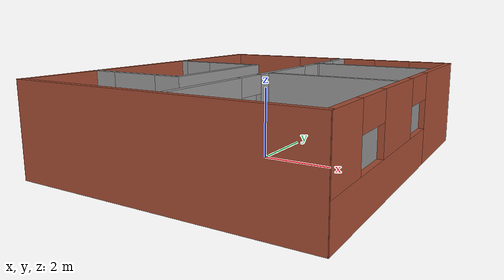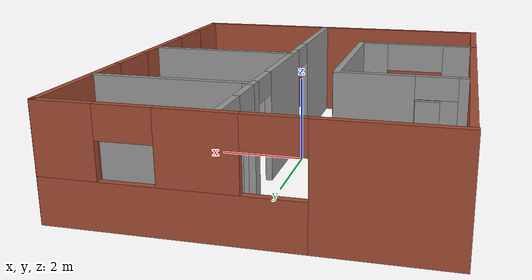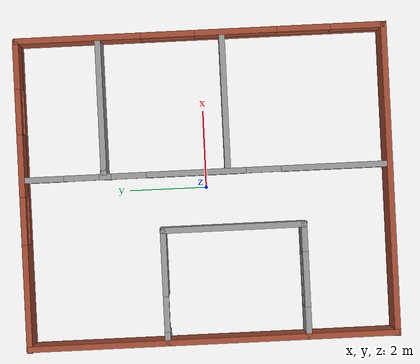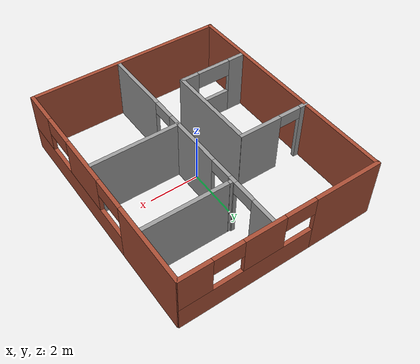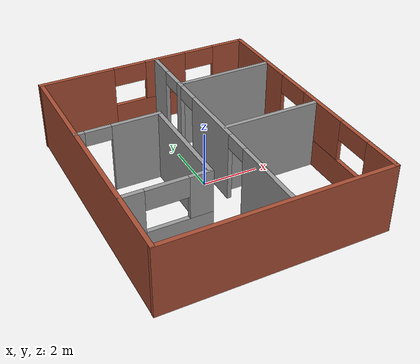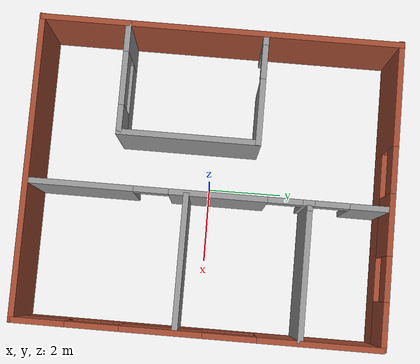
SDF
<?xml version='1.0'?>
<sdf version='1.7'>
  <model name='my_world_example'>
    <link name='Wall_14'>
      <pose>0.509968 2.60791 0 0 -0 0</pose>
      <self_collide>0</self_collide>
      <enable_wind>0</enable_wind>
      <kinematic>0</kinematic>
      <visual name='Wall_14_Visual'>
        <pose>0 0 1.25 0 -0 0</pose>
        <geometry>
          <box>
            <size>0.15 0.15 2.5</size>
          </box>
        </geometry>
        <material>
          <script>
            <uri>file://media/materials/scripts/gazebo.material</uri>
            <name>Gazebo/Grey</name>
          </script>
          <ambient>1 1 1 1</ambient>
          <shader type='pixel'/>
        </material>
        <meta>
          <layer>0</layer>
        </meta>
        <transparency>0</transparency>
        <cast_shadows>1</cast_shadows>
      </visual>
      <collision name='Wall_14_Collision'>
        <laser_retro>0</laser_retro>
        <max_contacts>10</max_contacts>
        <pose>0 0 1.25 0 -0 0</pose>
        <geometry>
          <box>
            <size>0.15 0.15 2.5</size>
          </box>
        </geometry>
        <surface>
          <friction>
            <ode>
              <mu>1</mu>
              <mu2>1</mu2>
              <fdir1>0 0 0</fdir1>
              <slip1>0</slip1>
              <slip2>0</slip2>
            </ode>
            <torsional>
              <coefficient>1</coefficient>
              <patch_radius>0</patch_radius>
              <surface_radius>0</surface_radius>
              <use_patch_radius>1</use_patch_radius>
              <ode>
                <slip>0</slip>
              </ode>
            </torsional>
          </friction>
          <bounce>
            <restitution_coefficient>0</restitution_coefficient>
            <threshold>1e+06</threshold>
          </bounce>
          <contact>
            <collide_without_contact>0</collide_without_contact>
            <collide_without_contact_bitmask>1</collide_without_contact_bitmask>
            <collide_bitmask>1</collide_bitmask>
            <ode>
              <soft_cfm>0</soft_cfm>
              <soft_erp>0.2</soft_erp>
              <kp>1e+13</kp>
              <kd>1</kd>
              <max_vel>0.01</max_vel>
              <min_depth>0</min_depth>
            </ode>
            <bullet>
              <split_impulse>1</split_impulse>
              <split_impulse_penetration_threshold>-0.01</split_impulse_penetration_threshold>
              <soft_cfm>0</soft_cfm>
              <soft_erp>0.2</soft_erp>
              <kp>1e+13</kp>
              <kd>1</kd>
            </bullet>
          </contact>
        </surface>
      </collision>
    </link>
    <link name='Wall_3'>
      <pose>3.93862 -0.015464 0 0 0 -1.5708</pose>
      <self_collide>0</self_collide>
      <enable_wind>0</enable_wind>
      <kinematic>0</kinematic>
      <visual name='Wall_3_Visual_4'>
        <pose>-0.833377 0 2.15 0 -0 0</pose>
        <geometry>
          <box>
            <size>1.378 0.15 0.7</size>
          </box>
        </geometry>
        <material>
          <script>
            <uri>file://media/materials/scripts/gazebo.material</uri>
            <name>Gazebo/Bricks</name>
          </script>
          <ambient>1 1 1 1</ambient>
          <shader type='pixel'/>
        </material>
        <meta>
          <layer>0</layer>
        </meta>
        <transparency>0</transparency>
        <cast_shadows>1</cast_shadows>
      </visual>
      <visual name='Wall_3_Visual_5'>
        <pose>2.64172 0 2.15 0 -0 0</pose>
        <geometry>
          <box>
            <size>1.37 0.15 0.7</size>
          </box>
        </geometry>
        <material>
          <script>
            <uri>file://media/materials/scripts/gazebo.material</uri>
            <name>Gazebo/Bricks</name>
          </script>
          <ambient>1 1 1 1</ambient>
          <shader type='pixel'/>
        </material>
        <meta>
          <layer>0</layer>
        </meta>
        <transparency>0</transparency>
        <cast_shadows>1</cast_shadows>
      </visual>
      <visual name='Wall_3_Visual_3'>
        <pose>4.03836 0 1.75 0 -0 0</pose>
        <geometry>
          <box>
            <size>1.42328 0.15 1.5</size>
          </box>
        </geometry>
        <material>
          <script>
            <uri>file://media/materials/scripts/gazebo.material</uri>
            <name>Gazebo/Bricks</name>
          </script>
          <ambient>1 1 1 1</ambient>
          <shader type='pixel'/>
        </material>
        <meta>
          <layer>0</layer>
        </meta>
        <transparency>0</transparency>
        <cast_shadows>1</cast_shadows>
      </visual>
      <visual name='Wall_3_Visual_1'>
        <pose>1.61381 0 0.5 0 -0 0</pose>
        <geometry>
          <box>
            <size>6.27238 0.15 1</size>
          </box>
        </geometry>
        <material>
          <script>
            <uri>file://media/materials/scripts/gazebo.material</uri>
            <name>Gazebo/Bricks</name>
          </script>
          <ambient>1 1 1 1</ambient>
          <shader type='pixel'/>
        </material>
        <meta>
          <layer>0</layer>
        </meta>
        <transparency>0</transparency>
        <cast_shadows>1</cast_shadows>
      </visual>
      <visual name='Wall_3_Visual_2'>
        <pose>0.90617 0 1.75 0 -0 0</pose>
        <geometry>
          <box>
            <size>2.10109 0.15 1.5</size>
          </box>
        </geometry>
        <material>
          <script>
            <uri>file://media/materials/scripts/gazebo.material</uri>
            <name>Gazebo/Bricks</name>
          </script>
          <ambient>1 1 1 1</ambient>
          <shader type='pixel'/>
        </material>
        <meta>
          <layer>0</layer>
        </meta>
        <transparency>0</transparency>
        <cast_shadows>1</cast_shadows>
      </visual>
      <visual name='Wall_3_Visual_0'>
        <pose>-3.13619 0 1.25 0 -0 0</pose>
        <geometry>
          <box>
            <size>3.22762 0.15 2.5</size>
          </box>
        </geometry>
        <material>
          <script>
            <uri>file://media/materials/scripts/gazebo.material</uri>
            <name>Gazebo/Bricks</name>
          </script>
          <ambient>1 1 1 1</ambient>
          <shader type='pixel'/>
        </material>
        <meta>
          <layer>0</layer>
        </meta>
        <transparency>0</transparency>
        <cast_shadows>1</cast_shadows>
      </visual>
      <collision name='Wall_3_Collision_5'>
        <laser_retro>0</laser_retro>
        <max_contacts>10</max_contacts>
        <pose>2.64172 0 2.15 0 -0 0</pose>
        <geometry>
          <box>
            <size>1.37 0.15 0.7</size>
          </box>
        </geometry>
        <surface>
          <friction>
            <ode>
              <mu>1</mu>
              <mu2>1</mu2>
              <fdir1>0 0 0</fdir1>
              <slip1>0</slip1>
              <slip2>0</slip2>
            </ode>
            <torsional>
              <coefficient>1</coefficient>
              <patch_radius>0</patch_radius>
              <surface_radius>0</surface_radius>
              <use_patch_radius>1</use_patch_radius>
              <ode>
                <slip>0</slip>
              </ode>
            </torsional>
          </friction>
          <bounce>
            <restitution_coefficient>0</restitution_coefficient>
            <threshold>1e+06</threshold>
          </bounce>
          <contact>
            <collide_without_contact>0</collide_without_contact>
            <collide_without_contact_bitmask>1</collide_without_contact_bitmask>
            <collide_bitmask>1</collide_bitmask>
            <ode>
              <soft_cfm>0</soft_cfm>
              <soft_erp>0.2</soft_erp>
              <kp>1e+13</kp>
              <kd>1</kd>
              <max_vel>0.01</max_vel>
              <min_depth>0</min_depth>
            </ode>
            <bullet>
              <split_impulse>1</split_impulse>
              <split_impulse_penetration_threshold>-0.01</split_impulse_penetration_threshold>
              <soft_cfm>0</soft_cfm>
              <soft_erp>0.2</soft_erp>
              <kp>1e+13</kp>
              <kd>1</kd>
            </bullet>
          </contact>
        </surface>
      </collision>
      <collision name='Wall_3_Collision_2'>
        <laser_retro>0</laser_retro>
        <max_contacts>10</max_contacts>
        <pose>0.90617 0 1.75 0 -0 0</pose>
        <geometry>
          <box>
            <size>2.10109 0.15 1.5</size>
          </box>
        </geometry>
        <surface>
          <friction>
            <ode>
              <mu>1</mu>
              <mu2>1</mu2>
              <fdir1>0 0 0</fdir1>
              <slip1>0</slip1>
              <slip2>0</slip2>
            </ode>
            <torsional>
              <coefficient>1</coefficient>
              <patch_radius>0</patch_radius>
              <surface_radius>0</surface_radius>
              <use_patch_radius>1</use_patch_radius>
              <ode>
                <slip>0</slip>
              </ode>
            </torsional>
          </friction>
          <bounce>
            <restitution_coefficient>0</restitution_coefficient>
            <threshold>1e+06</threshold>
          </bounce>
          <contact>
            <collide_without_contact>0</collide_without_contact>
            <collide_without_contact_bitmask>1</collide_without_contact_bitmask>
            <collide_bitmask>1</collide_bitmask>
            <ode>
              <soft_cfm>0</soft_cfm>
              <soft_erp>0.2</soft_erp>
              <kp>1e+13</kp>
              <kd>1</kd>
              <max_vel>0.01</max_vel>
              <min_depth>0</min_depth>
            </ode>
            <bullet>
              <split_impulse>1</split_impulse>
              <split_impulse_penetration_threshold>-0.01</split_impulse_penetration_threshold>
              <soft_cfm>0</soft_cfm>
              <soft_erp>0.2</soft_erp>
              <kp>1e+13</kp>
              <kd>1</kd>
            </bullet>
          </contact>
        </surface>
      </collision>
      <collision name='Wall_3_Collision_4'>
        <laser_retro>0</laser_retro>
        <max_contacts>10</max_contacts>
        <pose>-0.833377 0 2.15 0 -0 0</pose>
        <geometry>
          <box>
            <size>1.378 0.15 0.7</size>
          </box>
        </geometry>
        <surface>
          <friction>
            <ode>
              <mu>1</mu>
              <mu2>1</mu2>
              <fdir1>0 0 0</fdir1>
              <slip1>0</slip1>
              <slip2>0</slip2>
            </ode>
            <torsional>
              <coefficient>1</coefficient>
              <patch_radius>0</patch_radius>
              <surface_radius>0</surface_radius>
              <use_patch_radius>1</use_patch_radius>
              <ode>
                <slip>0</slip>
              </ode>
            </torsional>
          </friction>
          <bounce>
            <restitution_coefficient>0</restitution_coefficient>
            <threshold>1e+06</threshold>
          </bounce>
          <contact>
            <collide_without_contact>0</collide_without_contact>
            <collide_without_contact_bitmask>1</collide_without_contact_bitmask>
            <collide_bitmask>1</collide_bitmask>
            <ode>
              <soft_cfm>0</soft_cfm>
              <soft_erp>0.2</soft_erp>
              <kp>1e+13</kp>
              <kd>1</kd>
              <max_vel>0.01</max_vel>
              <min_depth>0</min_depth>
            </ode>
            <bullet>
              <split_impulse>1</split_impulse>
              <split_impulse_penetration_threshold>-0.01</split_impulse_penetration_threshold>
              <soft_cfm>0</soft_cfm>
              <soft_erp>0.2</soft_erp>
              <kp>1e+13</kp>
              <kd>1</kd>
            </bullet>
          </contact>
        </surface>
      </collision>
      <collision name='Wall_3_Collision_3'>
        <laser_retro>0</laser_retro>
        <max_contacts>10</max_contacts>
        <pose>4.03836 0 1.75 0 -0 0</pose>
        <geometry>
          <box>
            <size>1.42328 0.15 1.5</size>
          </box>
        </geometry>
        <surface>
          <friction>
            <ode>
              <mu>1</mu>
              <mu2>1</mu2>
              <fdir1>0 0 0</fdir1>
              <slip1>0</slip1>
              <slip2>0</slip2>
            </ode>
            <torsional>
              <coefficient>1</coefficient>
              <patch_radius>0</patch_radius>
              <surface_radius>0</surface_radius>
              <use_patch_radius>1</use_patch_radius>
              <ode>
                <slip>0</slip>
              </ode>
            </torsional>
          </friction>
          <bounce>
            <restitution_coefficient>0</restitution_coefficient>
            <threshold>1e+06</threshold>
          </bounce>
          <contact>
            <collide_without_contact>0</collide_without_contact>
            <collide_without_contact_bitmask>1</collide_without_contact_bitmask>
            <collide_bitmask>1</collide_bitmask>
            <ode>
              <soft_cfm>0</soft_cfm>
              <soft_erp>0.2</soft_erp>
              <kp>1e+13</kp>
              <kd>1</kd>
              <max_vel>0.01</max_vel>
              <min_depth>0</min_depth>
            </ode>
            <bullet>
              <split_impulse>1</split_impulse>
              <split_impulse_penetration_threshold>-0.01</split_impulse_penetration_threshold>
              <soft_cfm>0</soft_cfm>
              <soft_erp>0.2</soft_erp>
              <kp>1e+13</kp>
              <kd>1</kd>
            </bullet>
          </contact>
        </surface>
      </collision>
      <collision name='Wall_3_Collision_1'>
        <laser_retro>0</laser_retro>
        <max_contacts>10</max_contacts>
        <pose>1.61381 0 0.5 0 -0 0</pose>
        <geometry>
          <box>
            <size>6.27238 0.15 1</size>
          </box>
        </geometry>
        <surface>
          <friction>
            <ode>
              <mu>1</mu>
              <mu2>1</mu2>
              <fdir1>0 0 0</fdir1>
              <slip1>0</slip1>
              <slip2>0</slip2>
            </ode>
            <torsional>
              <coefficient>1</coefficient>
              <patch_radius>0</patch_radius>
              <surface_radius>0</surface_radius>
              <use_patch_radius>1</use_patch_radius>
              <ode>
                <slip>0</slip>
              </ode>
            </torsional>
          </friction>
          <bounce>
            <restitution_coefficient>0</restitution_coefficient>
            <threshold>1e+06</threshold>
          </bounce>
          <contact>
            <collide_without_contact>0</collide_without_contact>
            <collide_without_contact_bitmask>1</collide_without_contact_bitmask>
            <collide_bitmask>1</collide_bitmask>
            <ode>
              <soft_cfm>0</soft_cfm>
              <soft_erp>0.2</soft_erp>
              <kp>1e+13</kp>
              <kd>1</kd>
              <max_vel>0.01</max_vel>
              <min_depth>0</min_depth>
            </ode>
            <bullet>
              <split_impulse>1</split_impulse>
              <split_impulse_penetration_threshold>-0.01</split_impulse_penetration_threshold>
              <soft_cfm>0</soft_cfm>
              <soft_erp>0.2</soft_erp>
              <kp>1e+13</kp>
              <kd>1</kd>
            </bullet>
          </contact>
        </surface>
      </collision>
      <collision name='Wall_3_Collision_0'>
        <laser_retro>0</laser_retro>
        <max_contacts>10</max_contacts>
        <pose>-3.13619 0 1.25 0 -0 0</pose>
        <geometry>
          <box>
            <size>3.22762 0.15 2.5</size>
          </box>
        </geometry>
        <surface>
          <friction>
            <ode>
              <mu>1</mu>
              <mu2>1</mu2>
              <fdir1>0 0 0</fdir1>
              <slip1>0</slip1>
              <slip2>0</slip2>
            </ode>
            <torsional>
              <coefficient>1</coefficient>
              <patch_radius>0</patch_radius>
              <surface_radius>0</surface_radius>
              <use_patch_radius>1</use_patch_radius>
              <ode>
                <slip>0</slip>
              </ode>
            </torsional>
          </friction>
          <bounce>
            <restitution_coefficient>0</restitution_coefficient>
            <threshold>1e+06</threshold>
          </bounce>
          <contact>
            <collide_without_contact>0</collide_without_contact>
            <collide_without_contact_bitmask>1</collide_without_contact_bitmask>
            <collide_bitmask>1</collide_bitmask>
            <ode>
              <soft_cfm>0</soft_cfm>
              <soft_erp>0.2</soft_erp>
              <kp>1e+13</kp>
              <kd>1</kd>
              <max_vel>0.01</max_vel>
              <min_depth>0</min_depth>
            </ode>
            <bullet>
              <split_impulse>1</split_impulse>
              <split_impulse_penetration_threshold>-0.01</split_impulse_penetration_threshold>
              <soft_cfm>0</soft_cfm>
              <soft_erp>0.2</soft_erp>
              <kp>1e+13</kp>
              <kd>1</kd>
            </bullet>
          </contact>
        </surface>
      </collision>
    </link>
    <link name='Wall_33'>
      <pose>-3.92017 0.013616 0 0 0 -1.5708</pose>
      <self_collide>0</self_collide>
      <enable_wind>0</enable_wind>
      <kinematic>0</kinematic>
      <visual name='Wall_33_Visual'>
        <pose>0 0 1.25 0 -0 0</pose>
        <geometry>
          <box>
            <size>9.5 0.15 2.5</size>
          </box>
        </geometry>
        <material>
          <script>
            <uri>file://media/materials/scripts/gazebo.material</uri>
            <name>Gazebo/Bricks</name>
          </script>
          <ambient>1 1 1 1</ambient>
          <shader type='pixel'/>
        </material>
        <meta>
          <layer>0</layer>
        </meta>
        <transparency>0</transparency>
        <cast_shadows>1</cast_shadows>
      </visual>
      <collision name='Wall_33_Collision'>
        <laser_retro>0</laser_retro>
        <max_contacts>10</max_contacts>
        <pose>0 0 1.25 0 -0 0</pose>
        <geometry>
          <box>
            <size>9.5 0.15 2.5</size>
          </box>
        </geometry>
        <surface>
          <friction>
            <ode>
              <mu>1</mu>
              <mu2>1</mu2>
              <fdir1>0 0 0</fdir1>
              <slip1>0</slip1>
              <slip2>0</slip2>
            </ode>
            <torsional>
              <coefficient>1</coefficient>
              <patch_radius>0</patch_radius>
              <surface_radius>0</surface_radius>
              <use_patch_radius>1</use_patch_radius>
              <ode>
                <slip>0</slip>
              </ode>
            </torsional>
          </friction>
          <bounce>
            <restitution_coefficient>0</restitution_coefficient>
            <threshold>1e+06</threshold>
          </bounce>
          <contact>
            <collide_without_contact>0</collide_without_contact>
            <collide_without_contact_bitmask>1</collide_without_contact_bitmask>
            <collide_bitmask>1</collide_bitmask>
            <ode>
              <soft_cfm>0</soft_cfm>
              <soft_erp>0.2</soft_erp>
              <kp>1e+13</kp>
              <kd>1</kd>
              <max_vel>0.01</max_vel>
              <min_depth>0</min_depth>
            </ode>
            <bullet>
              <split_impulse>1</split_impulse>
              <split_impulse_penetration_threshold>-0.01</split_impulse_penetration_threshold>
              <soft_cfm>0</soft_cfm>
              <soft_erp>0.2</soft_erp>
              <kp>1e+13</kp>
              <kd>1</kd>
            </bullet>
          </contact>
        </surface>
      </collision>
    </link>
    <link name='Wall_35'>
      <pose>-2.48639 1.16661 0 0 -0 0</pose>
      <self_collide>0</self_collide>
      <enable_wind>0</enable_wind>
      <kinematic>0</kinematic>
      <visual name='Wall_35_Visual_1'>
        <pose>0.62567 0 1.25 0 -0 0</pose>
        <geometry>
          <box>
            <size>1.74866 0.15 2.5</size>
          </box>
        </geometry>
        <material>
          <script>
            <uri>file://media/materials/scripts/gazebo.material</uri>
            <name>Gazebo/Grey</name>
          </script>
          <ambient>1 1 1 1</ambient>
          <shader type='pixel'/>
        </material>
        <meta>
          <layer>0</layer>
        </meta>
        <transparency>0</transparency>
        <cast_shadows>1</cast_shadows>
      </visual>
      <visual name='Wall_35_Visual_0'>
        <pose>-1.32433 0 1.25 0 -0 0</pose>
        <geometry>
          <box>
            <size>0.35134 0.15 2.5</size>
          </box>
        </geometry>
        <material>
          <script>
            <uri>file://media/materials/scripts/gazebo.material</uri>
            <name>Gazebo/Grey</name>
          </script>
          <ambient>1 1 1 1</ambient>
          <shader type='pixel'/>
        </material>
        <meta>
          <layer>0</layer>
        </meta>
        <transparency>0</transparency>
        <cast_shadows>1</cast_shadows>
      </visual>
      <visual name='Wall_35_Visual_2'>
        <pose>-0.69866 0 2.25 0 -0 0</pose>
        <geometry>
          <box>
            <size>0.9 0.15 0.5</size>
          </box>
        </geometry>
        <material>
          <script>
            <uri>file://media/materials/scripts/gazebo.material</uri>
            <name>Gazebo/Grey</name>
          </script>
          <ambient>1 1 1 1</ambient>
          <shader type='pixel'/>
        </material>
        <meta>
          <layer>0</layer>
        </meta>
        <transparency>0</transparency>
        <cast_shadows>1</cast_shadows>
      </visual>
      <collision name='Wall_35_Collision_0'>
        <laser_retro>0</laser_retro>
        <max_contacts>10</max_contacts>
        <pose>-1.32433 0 1.25 0 -0 0</pose>
        <geometry>
          <box>
            <size>0.35134 0.15 2.5</size>
          </box>
        </geometry>
        <surface>
          <friction>
            <ode>
              <mu>1</mu>
              <mu2>1</mu2>
              <fdir1>0 0 0</fdir1>
              <slip1>0</slip1>
              <slip2>0</slip2>
            </ode>
            <torsional>
              <coefficient>1</coefficient>
              <patch_radius>0</patch_radius>
              <surface_radius>0</surface_radius>
              <use_patch_radius>1</use_patch_radius>
              <ode>
                <slip>0</slip>
              </ode>
            </torsional>
          </friction>
          <bounce>
            <restitution_coefficient>0</restitution_coefficient>
            <threshold>1e+06</threshold>
          </bounce>
          <contact>
            <collide_without_contact>0</collide_without_contact>
            <collide_without_contact_bitmask>1</collide_without_contact_bitmask>
            <collide_bitmask>1</collide_bitmask>
            <ode>
              <soft_cfm>0</soft_cfm>
              <soft_erp>0.2</soft_erp>
              <kp>1e+13</kp>
              <kd>1</kd>
              <max_vel>0.01</max_vel>
              <min_depth>0</min_depth>
            </ode>
            <bullet>
              <split_impulse>1</split_impulse>
              <split_impulse_penetration_threshold>-0.01</split_impulse_penetration_threshold>
              <soft_cfm>0</soft_cfm>
              <soft_erp>0.2</soft_erp>
              <kp>1e+13</kp>
              <kd>1</kd>
            </bullet>
          </contact>
        </surface>
      </collision>
      <collision name='Wall_35_Collision_2'>
        <laser_retro>0</laser_retro>
        <max_contacts>10</max_contacts>
        <pose>-0.69866 0 2.25 0 -0 0</pose>
        <geometry>
          <box>
            <size>0.9 0.15 0.5</size>
          </box>
        </geometry>
        <surface>
          <friction>
            <ode>
              <mu>1</mu>
              <mu2>1</mu2>
              <fdir1>0 0 0</fdir1>
              <slip1>0</slip1>
              <slip2>0</slip2>
            </ode>
            <torsional>
              <coefficient>1</coefficient>
              <patch_radius>0</patch_radius>
              <surface_radius>0</surface_radius>
              <use_patch_radius>1</use_patch_radius>
              <ode>
                <slip>0</slip>
              </ode>
            </torsional>
          </friction>
          <bounce>
            <restitution_coefficient>0</restitution_coefficient>
            <threshold>1e+06</threshold>
          </bounce>
          <contact>
            <collide_without_contact>0</collide_without_contact>
            <collide_without_contact_bitmask>1</collide_without_contact_bitmask>
            <collide_bitmask>1</collide_bitmask>
            <ode>
              <soft_cfm>0</soft_cfm>
              <soft_erp>0.2</soft_erp>
              <kp>1e+13</kp>
              <kd>1</kd>
              <max_vel>0.01</max_vel>
              <min_depth>0</min_depth>
            </ode>
            <bullet>
              <split_impulse>1</split_impulse>
              <split_impulse_penetration_threshold>-0.01</split_impulse_penetration_threshold>
              <soft_cfm>0</soft_cfm>
              <soft_erp>0.2</soft_erp>
              <kp>1e+13</kp>
              <kd>1</kd>
            </bullet>
          </contact>
        </surface>
      </collision>
      <collision name='Wall_35_Collision_1'>
        <laser_retro>0</laser_retro>
        <max_contacts>10</max_contacts>
        <pose>0.62567 0 1.25 0 -0 0</pose>
        <geometry>
          <box>
            <size>1.74866 0.15 2.5</size>
          </box>
        </geometry>
        <surface>
          <friction>
            <ode>
              <mu>1</mu>
              <mu2>1</mu2>
              <fdir1>0 0 0</fdir1>
              <slip1>0</slip1>
              <slip2>0</slip2>
            </ode>
            <torsional>
              <coefficient>1</coefficient>
              <patch_radius>0</patch_radius>
              <surface_radius>0</surface_radius>
              <use_patch_radius>1</use_patch_radius>
              <ode>
                <slip>0</slip>
              </ode>
            </torsional>
          </friction>
          <bounce>
            <restitution_coefficient>0</restitution_coefficient>
            <threshold>1e+06</threshold>
          </bounce>
          <contact>
            <collide_without_contact>0</collide_without_contact>
            <collide_without_contact_bitmask>1</collide_without_contact_bitmask>
            <collide_bitmask>1</collide_bitmask>
            <ode>
              <soft_cfm>0</soft_cfm>
              <soft_erp>0.2</soft_erp>
              <kp>1e+13</kp>
              <kd>1</kd>
              <max_vel>0.01</max_vel>
              <min_depth>0</min_depth>
            </ode>
            <bullet>
              <split_impulse>1</split_impulse>
              <split_impulse_penetration_threshold>-0.01</split_impulse_penetration_threshold>
              <soft_cfm>0</soft_cfm>
              <soft_erp>0.2</soft_erp>
              <kp>1e+13</kp>
              <kd>1</kd>
            </bullet>
          </contact>
        </surface>
      </collision>
    </link>
    <link name='Wall_38'>
      <pose>-0.013622 4.69452 0 0 -0 0</pose>
      <self_collide>0</self_collide>
      <enable_wind>0</enable_wind>
      <kinematic>0</kinematic>
      <visual name='Wall_38_Visual_4'>
        <pose>-0.631709 0 2.15 0 -0 0</pose>
        <geometry>
          <box>
            <size>1.221 0.15 0.7</size>
          </box>
        </geometry>
        <material>
          <script>
            <uri>file://media/materials/scripts/gazebo.material</uri>
            <name>Gazebo/Bricks</name>
          </script>
          <ambient>1 1 1 1</ambient>
          <shader type='pixel'/>
        </material>
        <meta>
          <layer>0</layer>
        </meta>
        <transparency>0</transparency>
        <cast_shadows>1</cast_shadows>
      </visual>
      <visual name='Wall_38_Visual_5'>
        <pose>2.15803 0 2.15 0 -0 0</pose>
        <geometry>
          <box>
            <size>1.163 0.15 0.7</size>
          </box>
        </geometry>
        <material>
          <script>
            <uri>file://media/materials/scripts/gazebo.material</uri>
            <name>Gazebo/Bricks</name>
          </script>
          <ambient>1 1 1 1</ambient>
          <shader type='pixel'/>
        </material>
        <meta>
          <layer>0</layer>
        </meta>
        <transparency>0</transparency>
        <cast_shadows>1</cast_shadows>
      </visual>
      <visual name='Wall_38_Visual_1'>
        <pose>1.3789 0 0.5 0 -0 0</pose>
        <geometry>
          <box>
            <size>5.24221 0.15 1</size>
          </box>
        </geometry>
        <material>
          <script>
            <uri>file://media/materials/scripts/gazebo.material</uri>
            <name>Gazebo/Bricks</name>
          </script>
          <ambient>1 1 1 1</ambient>
          <shader type='pixel'/>
        </material>
        <meta>
          <layer>0</layer>
        </meta>
        <transparency>0</transparency>
        <cast_shadows>1</cast_shadows>
      </visual>
      <visual name='Wall_38_Visual_2'>
        <pose>0.777661 0 1.75 0 -0 0</pose>
        <geometry>
          <box>
            <size>1.59774 0.15 1.5</size>
          </box>
        </geometry>
        <material>
          <script>
            <uri>file://media/materials/scripts/gazebo.material</uri>
            <name>Gazebo/Bricks</name>
          </script>
          <ambient>1 1 1 1</ambient>
          <shader type='pixel'/>
        </material>
        <meta>
          <layer>0</layer>
        </meta>
        <transparency>0</transparency>
        <cast_shadows>1</cast_shadows>
      </visual>
      <visual name='Wall_38_Visual_3'>
        <pose>3.36977 0 1.75 0 -0 0</pose>
        <geometry>
          <box>
            <size>1.26047 0.15 1.5</size>
          </box>
        </geometry>
        <material>
          <script>
            <uri>file://media/materials/scripts/gazebo.material</uri>
            <name>Gazebo/Bricks</name>
          </script>
          <ambient>1 1 1 1</ambient>
          <shader type='pixel'/>
        </material>
        <meta>
          <layer>0</layer>
        </meta>
        <transparency>0</transparency>
        <cast_shadows>1</cast_shadows>
      </visual>
      <visual name='Wall_38_Visual_0'>
        <pose>-2.6211 0 1.25 0 -0 0</pose>
        <geometry>
          <box>
            <size>2.75779 0.15 2.5</size>
          </box>
        </geometry>
        <material>
          <script>
            <uri>file://media/materials/scripts/gazebo.material</uri>
            <name>Gazebo/Bricks</name>
          </script>
          <ambient>1 1 1 1</ambient>
          <shader type='pixel'/>
        </material>
        <meta>
          <layer>0</layer>
        </meta>
        <transparency>0</transparency>
        <cast_shadows>1</cast_shadows>
      </visual>
      <collision name='Wall_38_Collision_4'>
        <laser_retro>0</laser_retro>
        <max_contacts>10</max_contacts>
        <pose>-0.631709 0 2.15 0 -0 0</pose>
        <geometry>
          <box>
            <size>1.221 0.15 0.7</size>
          </box>
        </geometry>
        <surface>
          <friction>
            <ode>
              <mu>1</mu>
              <mu2>1</mu2>
              <fdir1>0 0 0</fdir1>
              <slip1>0</slip1>
              <slip2>0</slip2>
            </ode>
            <torsional>
              <coefficient>1</coefficient>
              <patch_radius>0</patch_radius>
              <surface_radius>0</surface_radius>
              <use_patch_radius>1</use_patch_radius>
              <ode>
                <slip>0</slip>
              </ode>
            </torsional>
          </friction>
          <bounce>
            <restitution_coefficient>0</restitution_coefficient>
            <threshold>1e+06</threshold>
          </bounce>
          <contact>
            <collide_without_contact>0</collide_without_contact>
            <collide_without_contact_bitmask>1</collide_without_contact_bitmask>
            <collide_bitmask>1</collide_bitmask>
            <ode>
              <soft_cfm>0</soft_cfm>
              <soft_erp>0.2</soft_erp>
              <kp>1e+13</kp>
              <kd>1</kd>
              <max_vel>0.01</max_vel>
              <min_depth>0</min_depth>
            </ode>
            <bullet>
              <split_impulse>1</split_impulse>
              <split_impulse_penetration_threshold>-0.01</split_impulse_penetration_threshold>
              <soft_cfm>0</soft_cfm>
              <soft_erp>0.2</soft_erp>
              <kp>1e+13</kp>
              <kd>1</kd>
            </bullet>
          </contact>
        </surface>
      </collision>
      <collision name='Wall_38_Collision_2'>
        <laser_retro>0</laser_retro>
        <max_contacts>10</max_contacts>
        <pose>0.777661 0 1.75 0 -0 0</pose>
        <geometry>
          <box>
            <size>1.59774 0.15 1.5</size>
          </box>
        </geometry>
        <surface>
          <friction>
            <ode>
              <mu>1</mu>
              <mu2>1</mu2>
              <fdir1>0 0 0</fdir1>
              <slip1>0</slip1>
              <slip2>0</slip2>
            </ode>
            <torsional>
              <coefficient>1</coefficient>
              <patch_radius>0</patch_radius>
              <surface_radius>0</surface_radius>
              <use_patch_radius>1</use_patch_radius>
              <ode>
                <slip>0</slip>
              </ode>
            </torsional>
          </friction>
          <bounce>
            <restitution_coefficient>0</restitution_coefficient>
            <threshold>1e+06</threshold>
          </bounce>
          <contact>
            <collide_without_contact>0</collide_without_contact>
            <collide_without_contact_bitmask>1</collide_without_contact_bitmask>
            <collide_bitmask>1</collide_bitmask>
            <ode>
              <soft_cfm>0</soft_cfm>
              <soft_erp>0.2</soft_erp>
              <kp>1e+13</kp>
              <kd>1</kd>
              <max_vel>0.01</max_vel>
              <min_depth>0</min_depth>
            </ode>
            <bullet>
              <split_impulse>1</split_impulse>
              <split_impulse_penetration_threshold>-0.01</split_impulse_penetration_threshold>
              <soft_cfm>0</soft_cfm>
              <soft_erp>0.2</soft_erp>
              <kp>1e+13</kp>
              <kd>1</kd>
            </bullet>
          </contact>
        </surface>
      </collision>
      <collision name='Wall_38_Collision_1'>
        <laser_retro>0</laser_retro>
        <max_contacts>10</max_contacts>
        <pose>1.3789 0 0.5 0 -0 0</pose>
        <geometry>
          <box>
            <size>5.24221 0.15 1</size>
          </box>
        </geometry>
        <surface>
          <friction>
            <ode>
              <mu>1</mu>
              <mu2>1</mu2>
              <fdir1>0 0 0</fdir1>
              <slip1>0</slip1>
              <slip2>0</slip2>
            </ode>
            <torsional>
              <coefficient>1</coefficient>
              <patch_radius>0</patch_radius>
              <surface_radius>0</surface_radius>
              <use_patch_radius>1</use_patch_radius>
              <ode>
                <slip>0</slip>
              </ode>
            </torsional>
          </friction>
          <bounce>
            <restitution_coefficient>0</restitution_coefficient>
            <threshold>1e+06</threshold>
          </bounce>
          <contact>
            <collide_without_contact>0</collide_without_contact>
            <collide_without_contact_bitmask>1</collide_without_contact_bitmask>
            <collide_bitmask>1</collide_bitmask>
            <ode>
              <soft_cfm>0</soft_cfm>
              <soft_erp>0.2</soft_erp>
              <kp>1e+13</kp>
              <kd>1</kd>
              <max_vel>0.01</max_vel>
              <min_depth>0</min_depth>
            </ode>
            <bullet>
              <split_impulse>1</split_impulse>
              <split_impulse_penetration_threshold>-0.01</split_impulse_penetration_threshold>
              <soft_cfm>0</soft_cfm>
              <soft_erp>0.2</soft_erp>
              <kp>1e+13</kp>
              <kd>1</kd>
            </bullet>
          </contact>
        </surface>
      </collision>
      <collision name='Wall_38_Collision_5'>
        <laser_retro>0</laser_retro>
        <max_contacts>10</max_contacts>
        <pose>2.15803 0 2.15 0 -0 0</pose>
        <geometry>
          <box>
            <size>1.163 0.15 0.7</size>
          </box>
        </geometry>
        <surface>
          <friction>
            <ode>
              <mu>1</mu>
              <mu2>1</mu2>
              <fdir1>0 0 0</fdir1>
              <slip1>0</slip1>
              <slip2>0</slip2>
            </ode>
            <torsional>
              <coefficient>1</coefficient>
              <patch_radius>0</patch_radius>
              <surface_radius>0</surface_radius>
              <use_patch_radius>1</use_patch_radius>
              <ode>
                <slip>0</slip>
              </ode>
            </torsional>
          </friction>
          <bounce>
            <restitution_coefficient>0</restitution_coefficient>
            <threshold>1e+06</threshold>
          </bounce>
          <contact>
            <collide_without_contact>0</collide_without_contact>
            <collide_without_contact_bitmask>1</collide_without_contact_bitmask>
            <collide_bitmask>1</collide_bitmask>
            <ode>
              <soft_cfm>0</soft_cfm>
              <soft_erp>0.2</soft_erp>
              <kp>1e+13</kp>
              <kd>1</kd>
              <max_vel>0.01</max_vel>
              <min_depth>0</min_depth>
            </ode>
            <bullet>
              <split_impulse>1</split_impulse>
              <split_impulse_penetration_threshold>-0.01</split_impulse_penetration_threshold>
              <soft_cfm>0</soft_cfm>
              <soft_erp>0.2</soft_erp>
              <kp>1e+13</kp>
              <kd>1</kd>
            </bullet>
          </contact>
        </surface>
      </collision>
      <collision name='Wall_38_Collision_3'>
        <laser_retro>0</laser_retro>
        <max_contacts>10</max_contacts>
        <pose>3.36977 0 1.75 0 -0 0</pose>
        <geometry>
          <box>
            <size>1.26047 0.15 1.5</size>
          </box>
        </geometry>
        <surface>
          <friction>
            <ode>
              <mu>1</mu>
              <mu2>1</mu2>
              <fdir1>0 0 0</fdir1>
              <slip1>0</slip1>
              <slip2>0</slip2>
            </ode>
            <torsional>
              <coefficient>1</coefficient>
              <patch_radius>0</patch_radius>
              <surface_radius>0</surface_radius>
              <use_patch_radius>1</use_patch_radius>
              <ode>
                <slip>0</slip>
              </ode>
            </torsional>
          </friction>
          <bounce>
            <restitution_coefficient>0</restitution_coefficient>
            <threshold>1e+06</threshold>
          </bounce>
          <contact>
            <collide_without_contact>0</collide_without_contact>
            <collide_without_contact_bitmask>1</collide_without_contact_bitmask>
            <collide_bitmask>1</collide_bitmask>
            <ode>
              <soft_cfm>0</soft_cfm>
              <soft_erp>0.2</soft_erp>
              <kp>1e+13</kp>
              <kd>1</kd>
              <max_vel>0.01</max_vel>
              <min_depth>0</min_depth>
            </ode>
            <bullet>
              <split_impulse>1</split_impulse>
              <split_impulse_penetration_threshold>-0.01</split_impulse_penetration_threshold>
              <soft_cfm>0</soft_cfm>
              <soft_erp>0.2</soft_erp>
              <kp>1e+13</kp>
              <kd>1</kd>
            </bullet>
          </contact>
        </surface>
      </collision>
      <collision name='Wall_38_Collision_0'>
        <laser_retro>0</laser_retro>
        <max_contacts>10</max_contacts>
        <pose>-2.6211 0 1.25 0 -0 0</pose>
        <geometry>
          <box>
            <size>2.75779 0.15 2.5</size>
          </box>
        </geometry>
        <surface>
          <friction>
            <ode>
              <mu>1</mu>
              <mu2>1</mu2>
              <fdir1>0 0 0</fdir1>
              <slip1>0</slip1>
              <slip2>0</slip2>
            </ode>
            <torsional>
              <coefficient>1</coefficient>
              <patch_radius>0</patch_radius>
              <surface_radius>0</surface_radius>
              <use_patch_radius>1</use_patch_radius>
              <ode>
                <slip>0</slip>
              </ode>
            </torsional>
          </friction>
          <bounce>
            <restitution_coefficient>0</restitution_coefficient>
            <threshold>1e+06</threshold>
          </bounce>
          <contact>
            <collide_without_contact>0</collide_without_contact>
            <collide_without_contact_bitmask>1</collide_without_contact_bitmask>
            <collide_bitmask>1</collide_bitmask>
            <ode>
              <soft_cfm>0</soft_cfm>
              <soft_erp>0.2</soft_erp>
              <kp>1e+13</kp>
              <kd>1</kd>
              <max_vel>0.01</max_vel>
              <min_depth>0</min_depth>
            </ode>
            <bullet>
              <split_impulse>1</split_impulse>
              <split_impulse_penetration_threshold>-0.01</split_impulse_penetration_threshold>
              <soft_cfm>0</soft_cfm>
              <soft_erp>0.2</soft_erp>
              <kp>1e+13</kp>
              <kd>1</kd>
            </bullet>
          </contact>
        </surface>
      </collision>
    </link>
    <link name='Wall_42'>
      <pose>0.387902 0.000987 0 0 0 -1.5708</pose>
      <self_collide>0</self_collide>
      <enable_wind>0</enable_wind>
      <kinematic>0</kinematic>
      <gravity>1</gravity>
      <inertial>
        <mass>1</mass>
        <pose>0 0 0 0 -0 0</pose>
        <inertia>
          <ixx>1</ixx>
          <ixy>0</ixy>
          <ixz>0</ixz>
          <iyy>1</iyy>
          <iyz>0</iyz>
          <izz>1</izz>
        </inertia>
      </inertial>
      <visual name='Wall_42_Visual_0'>
        <pose>-4.12408 0 1.25 0 -0 0</pose>
        <geometry>
          <box>
            <size>1.00184 0.15 2.5</size>
          </box>
        </geometry>
        <material>
          <script>
            <uri>file://media/materials/scripts/gazebo.material</uri>
            <name>Gazebo/Grey</name>
          </script>
          <ambient>1 1 1 1</ambient>
          <shader type='pixel'>
            <normal_map>__default__</normal_map>
          </shader>
        </material>
        <meta>
          <layer>0</layer>
        </meta>
        <transparency>0</transparency>
        <cast_shadows>1</cast_shadows>
      </visual>
      <visual name='Wall_42_Visual_1'>
        <pose>-2.5695 0 1.25 0 -0 0</pose>
        <geometry>
          <box>
            <size>0.307325 0.15 2.5</size>
          </box>
        </geometry>
        <material>
          <script>
            <uri>file://media/materials/scripts/gazebo.material</uri>
            <name>Gazebo/Grey</name>
          </script>
          <ambient>1 1 1 1</ambient>
          <shader type='pixel'>
            <normal_map>__default__</normal_map>
          </shader>
        </material>
        <meta>
          <layer>0</layer>
        </meta>
        <transparency>0</transparency>
        <cast_shadows>1</cast_shadows>
      </visual>
      <visual name='Wall_42_Visual_4'>
        <pose>-3.17316 0 2.25 0 -0 0</pose>
        <geometry>
          <box>
            <size>0.9 0.15 0.5</size>
          </box>
        </geometry>
        <material>
          <script>
            <uri>file://media/materials/scripts/gazebo.material</uri>
            <name>Gazebo/Grey</name>
          </script>
          <ambient>1 1 1 1</ambient>
          <shader type='pixel'>
            <normal_map>__default__</normal_map>
          </shader>
        </material>
        <meta>
          <layer>0</layer>
        </meta>
        <transparency>0</transparency>
        <cast_shadows>1</cast_shadows>
      </visual>
      <visual name='Wall_42_Visual_5'>
        <pose>-1.96584 0 2.25 0 -0 0</pose>
        <geometry>
          <box>
            <size>0.9 0.15 0.5</size>
          </box>
        </geometry>
        <material>
          <script>
            <uri>file://media/materials/scripts/gazebo.material</uri>
            <name>Gazebo/Grey</name>
          </script>
          <ambient>1 1 1 1</ambient>
          <shader type='pixel'>
            <normal_map>__default__</normal_map>
          </shader>
        </material>
        <meta>
          <layer>0</layer>
        </meta>
        <transparency>0</transparency>
        <cast_shadows>1</cast_shadows>
      </visual>
      <visual name='Wall_42_Visual_6'>
        <pose>1.47532 0 2.25 0 -0 0</pose>
        <geometry>
          <box>
            <size>0.9 0.15 0.5</size>
          </box>
        </geometry>
        <material>
          <script>
            <uri>file://media/materials/scripts/gazebo.material</uri>
            <name>Gazebo/Grey</name>
          </script>
          <ambient>1 1 1 1</ambient>
          <shader type='pixel'>
            <normal_map>__default__</normal_map>
          </shader>
        </material>
        <meta>
          <layer>0</layer>
        </meta>
        <transparency>0</transparency>
        <cast_shadows>1</cast_shadows>
      </visual>
      <visual name='Wall_42_Visual_3'>
        <pose>3.27516 0 1.25 0 -0 0</pose>
        <geometry>
          <box>
            <size>2.69968 0.15 2.5</size>
          </box>
        </geometry>
        <material>
          <script>
            <uri>file://media/materials/scripts/gazebo.material</uri>
            <name>Gazebo/Grey</name>
          </script>
          <ambient>1 1 1 1</ambient>
          <shader type='pixel'>
            <normal_map>__default__</normal_map>
          </shader>
        </material>
        <meta>
          <layer>0</layer>
        </meta>
        <transparency>0</transparency>
        <cast_shadows>1</cast_shadows>
      </visual>
      <visual name='Wall_42_Visual_2'>
        <pose>-0.245259 0 1.25 0 -0 0</pose>
        <geometry>
          <box>
            <size>2.54116 0.15 2.5</size>
          </box>
        </geometry>
        <material>
          <script>
            <uri>file://media/materials/scripts/gazebo.material</uri>
            <name>Gazebo/Grey</name>
          </script>
          <ambient>1 1 1 1</ambient>
          <shader type='pixel'>
            <normal_map>__default__</normal_map>
          </shader>
        </material>
        <meta>
          <layer>0</layer>
        </meta>
        <transparency>0</transparency>
        <cast_shadows>1</cast_shadows>
      </visual>
      <collision name='Wall_42_Collision_5'>
        <laser_retro>0</laser_retro>
        <max_contacts>10</max_contacts>
        <pose>-1.96584 0 2.25 0 -0 0</pose>
        <geometry>
          <box>
            <size>0.9 0.15 0.5</size>
          </box>
        </geometry>
        <surface>
          <friction>
            <ode>
              <mu>1</mu>
              <mu2>1</mu2>
              <fdir1>0 0 0</fdir1>
              <slip1>0</slip1>
              <slip2>0</slip2>
            </ode>
            <torsional>
              <coefficient>1</coefficient>
              <patch_radius>0</patch_radius>
              <surface_radius>0</surface_radius>
              <use_patch_radius>1</use_patch_radius>
              <ode>
                <slip>0</slip>
              </ode>
            </torsional>
          </friction>
          <bounce>
            <restitution_coefficient>0</restitution_coefficient>
            <threshold>1e+06</threshold>
          </bounce>
          <contact>
            <collide_without_contact>0</collide_without_contact>
            <collide_without_contact_bitmask>1</collide_without_contact_bitmask>
            <collide_bitmask>1</collide_bitmask>
            <ode>
              <soft_cfm>0</soft_cfm>
              <soft_erp>0.2</soft_erp>
              <kp>1e+13</kp>
              <kd>1</kd>
              <max_vel>0.01</max_vel>
              <min_depth>0</min_depth>
            </ode>
            <bullet>
              <split_impulse>1</split_impulse>
              <split_impulse_penetration_threshold>-0.01</split_impulse_penetration_threshold>
              <soft_cfm>0</soft_cfm>
              <soft_erp>0.2</soft_erp>
              <kp>1e+13</kp>
              <kd>1</kd>
            </bullet>
          </contact>
        </surface>
      </collision>
      <collision name='Wall_42_Collision_2'>
        <laser_retro>0</laser_retro>
        <max_contacts>10</max_contacts>
        <pose>-0.245259 0 1.25 0 -0 0</pose>
        <geometry>
          <box>
            <size>2.54116 0.15 2.5</size>
          </box>
        </geometry>
        <surface>
          <friction>
            <ode>
              <mu>1</mu>
              <mu2>1</mu2>
              <fdir1>0 0 0</fdir1>
              <slip1>0</slip1>
              <slip2>0</slip2>
            </ode>
            <torsional>
              <coefficient>1</coefficient>
              <patch_radius>0</patch_radius>
              <surface_radius>0</surface_radius>
              <use_patch_radius>1</use_patch_radius>
              <ode>
                <slip>0</slip>
              </ode>
            </torsional>
          </friction>
          <bounce>
            <restitution_coefficient>0</restitution_coefficient>
            <threshold>1e+06</threshold>
          </bounce>
          <contact>
            <collide_without_contact>0</collide_without_contact>
            <collide_without_contact_bitmask>1</collide_without_contact_bitmask>
            <collide_bitmask>1</collide_bitmask>
            <ode>
              <soft_cfm>0</soft_cfm>
              <soft_erp>0.2</soft_erp>
              <kp>1e+13</kp>
              <kd>1</kd>
              <max_vel>0.01</max_vel>
              <min_depth>0</min_depth>
            </ode>
            <bullet>
              <split_impulse>1</split_impulse>
              <split_impulse_penetration_threshold>-0.01</split_impulse_penetration_threshold>
              <soft_cfm>0</soft_cfm>
              <soft_erp>0.2</soft_erp>
              <kp>1e+13</kp>
              <kd>1</kd>
            </bullet>
          </contact>
        </surface>
      </collision>
      <collision name='Wall_42_Collision_0'>
        <laser_retro>0</laser_retro>
        <max_contacts>10</max_contacts>
        <pose>-4.12408 0 1.25 0 -0 0</pose>
        <geometry>
          <box>
            <size>1.00184 0.15 2.5</size>
          </box>
        </geometry>
        <surface>
          <friction>
            <ode>
              <mu>1</mu>
              <mu2>1</mu2>
              <fdir1>0 0 0</fdir1>
              <slip1>0</slip1>
              <slip2>0</slip2>
            </ode>
            <torsional>
              <coefficient>1</coefficient>
              <patch_radius>0</patch_radius>
              <surface_radius>0</surface_radius>
              <use_patch_radius>1</use_patch_radius>
              <ode>
                <slip>0</slip>
              </ode>
            </torsional>
          </friction>
          <bounce>
            <restitution_coefficient>0</restitution_coefficient>
            <threshold>1e+06</threshold>
          </bounce>
          <contact>
            <collide_without_contact>0</collide_without_contact>
            <collide_without_contact_bitmask>1</collide_without_contact_bitmask>
            <collide_bitmask>1</collide_bitmask>
            <ode>
              <soft_cfm>0</soft_cfm>
              <soft_erp>0.2</soft_erp>
              <kp>1e+13</kp>
              <kd>1</kd>
              <max_vel>0.01</max_vel>
              <min_depth>0</min_depth>
            </ode>
            <bullet>
              <split_impulse>1</split_impulse>
              <split_impulse_penetration_threshold>-0.01</split_impulse_penetration_threshold>
              <soft_cfm>0</soft_cfm>
              <soft_erp>0.2</soft_erp>
              <kp>1e+13</kp>
              <kd>1</kd>
            </bullet>
          </contact>
        </surface>
      </collision>
      <collision name='Wall_42_Collision_3'>
        <laser_retro>0</laser_retro>
        <max_contacts>10</max_contacts>
        <pose>3.27516 0 1.25 0 -0 0</pose>
        <geometry>
          <box>
            <size>2.69968 0.15 2.5</size>
          </box>
        </geometry>
        <surface>
          <friction>
            <ode>
              <mu>1</mu>
              <mu2>1</mu2>
              <fdir1>0 0 0</fdir1>
              <slip1>0</slip1>
              <slip2>0</slip2>
            </ode>
            <torsional>
              <coefficient>1</coefficient>
              <patch_radius>0</patch_radius>
              <surface_radius>0</surface_radius>
              <use_patch_radius>1</use_patch_radius>
              <ode>
                <slip>0</slip>
              </ode>
            </torsional>
          </friction>
          <bounce>
            <restitution_coefficient>0</restitution_coefficient>
            <threshold>1e+06</threshold>
          </bounce>
          <contact>
            <collide_without_contact>0</collide_without_contact>
            <collide_without_contact_bitmask>1</collide_without_contact_bitmask>
            <collide_bitmask>1</collide_bitmask>
            <ode>
              <soft_cfm>0</soft_cfm>
              <soft_erp>0.2</soft_erp>
              <kp>1e+13</kp>
              <kd>1</kd>
              <max_vel>0.01</max_vel>
              <min_depth>0</min_depth>
            </ode>
            <bullet>
              <split_impulse>1</split_impulse>
              <split_impulse_penetration_threshold>-0.01</split_impulse_penetration_threshold>
              <soft_cfm>0</soft_cfm>
              <soft_erp>0.2</soft_erp>
              <kp>1e+13</kp>
              <kd>1</kd>
            </bullet>
          </contact>
        </surface>
      </collision>
      <collision name='Wall_42_Collision_4'>
        <laser_retro>0</laser_retro>
        <max_contacts>10</max_contacts>
        <pose>-3.17316 0 2.25 0 -0 0</pose>
        <geometry>
          <box>
            <size>0.9 0.15 0.5</size>
          </box>
        </geometry>
        <surface>
          <friction>
            <ode>
              <mu>1</mu>
              <mu2>1</mu2>
              <fdir1>0 0 0</fdir1>
              <slip1>0</slip1>
              <slip2>0</slip2>
            </ode>
            <torsional>
              <coefficient>1</coefficient>
              <patch_radius>0</patch_radius>
              <surface_radius>0</surface_radius>
              <use_patch_radius>1</use_patch_radius>
              <ode>
                <slip>0</slip>
              </ode>
            </torsional>
          </friction>
          <bounce>
            <restitution_coefficient>0</restitution_coefficient>
            <threshold>1e+06</threshold>
          </bounce>
          <contact>
            <collide_without_contact>0</collide_without_contact>
            <collide_without_contact_bitmask>1</collide_without_contact_bitmask>
            <collide_bitmask>1</collide_bitmask>
            <ode>
              <soft_cfm>0</soft_cfm>
              <soft_erp>0.2</soft_erp>
              <kp>1e+13</kp>
              <kd>1</kd>
              <max_vel>0.01</max_vel>
              <min_depth>0</min_depth>
            </ode>
            <bullet>
              <split_impulse>1</split_impulse>
              <split_impulse_penetration_threshold>-0.01</split_impulse_penetration_threshold>
              <soft_cfm>0</soft_cfm>
              <soft_erp>0.2</soft_erp>
              <kp>1e+13</kp>
              <kd>1</kd>
            </bullet>
          </contact>
        </surface>
      </collision>
      <collision name='Wall_42_Collision_1'>
        <laser_retro>0</laser_retro>
        <max_contacts>10</max_contacts>
        <pose>-2.5695 0 1.25 0 -0 0</pose>
        <geometry>
          <box>
            <size>0.307325 0.15 2.5</size>
          </box>
        </geometry>
        <surface>
          <friction>
            <ode>
              <mu>1</mu>
              <mu2>1</mu2>
              <fdir1>0 0 0</fdir1>
              <slip1>0</slip1>
              <slip2>0</slip2>
            </ode>
            <torsional>
              <coefficient>1</coefficient>
              <patch_radius>0</patch_radius>
              <surface_radius>0</surface_radius>
              <use_patch_radius>1</use_patch_radius>
              <ode>
                <slip>0</slip>
              </ode>
            </torsional>
          </friction>
          <bounce>
            <restitution_coefficient>0</restitution_coefficient>
            <threshold>1e+06</threshold>
          </bounce>
          <contact>
            <collide_without_contact>0</collide_without_contact>
            <collide_without_contact_bitmask>1</collide_without_contact_bitmask>
            <collide_bitmask>1</collide_bitmask>
            <ode>
              <soft_cfm>0</soft_cfm>
              <soft_erp>0.2</soft_erp>
              <kp>1e+13</kp>
              <kd>1</kd>
              <max_vel>0.01</max_vel>
              <min_depth>0</min_depth>
            </ode>
            <bullet>
              <split_impulse>1</split_impulse>
              <split_impulse_penetration_threshold>-0.01</split_impulse_penetration_threshold>
              <soft_cfm>0</soft_cfm>
              <soft_erp>0.2</soft_erp>
              <kp>1e+13</kp>
              <kd>1</kd>
            </bullet>
          </contact>
        </surface>
      </collision>
      <collision name='Wall_42_Collision_6'>
        <laser_retro>0</laser_retro>
        <max_contacts>10</max_contacts>
        <pose>1.47532 0 2.25 0 -0 0</pose>
        <geometry>
          <box>
            <size>0.9 0.15 0.5</size>
          </box>
        </geometry>
        <surface>
          <friction>
            <ode>
              <mu>1</mu>
              <mu2>1</mu2>
              <fdir1>0 0 0</fdir1>
              <slip1>0</slip1>
              <slip2>0</slip2>
            </ode>
            <torsional>
              <coefficient>1</coefficient>
              <patch_radius>0</patch_radius>
              <surface_radius>0</surface_radius>
              <use_patch_radius>1</use_patch_radius>
              <ode>
                <slip>0</slip>
              </ode>
            </torsional>
          </friction>
          <bounce>
            <restitution_coefficient>0</restitution_coefficient>
            <threshold>1e+06</threshold>
          </bounce>
          <contact>
            <collide_without_contact>0</collide_without_contact>
            <collide_without_contact_bitmask>1</collide_without_contact_bitmask>
            <collide_bitmask>1</collide_bitmask>
            <ode>
              <soft_cfm>0</soft_cfm>
              <soft_erp>0.2</soft_erp>
              <kp>1e+13</kp>
              <kd>1</kd>
              <max_vel>0.01</max_vel>
              <min_depth>0</min_depth>
            </ode>
            <bullet>
              <split_impulse>1</split_impulse>
              <split_impulse_penetration_threshold>-0.01</split_impulse_penetration_threshold>
              <soft_cfm>0</soft_cfm>
              <soft_erp>0.2</soft_erp>
              <kp>1e+13</kp>
              <kd>1</kd>
            </bullet>
          </contact>
        </surface>
      </collision>
    </link>
    <link name='Wall_45'>
      <pose>-1.05416 -0.637427 0 0 -0 1.5708</pose>
      <self_collide>0</self_collide>
      <enable_wind>0</enable_wind>
      <kinematic>0</kinematic>
      <visual name='Wall_45_Visual'>
        <pose>0 0 1.25 0 -0 0</pose>
        <geometry>
          <box>
            <size>3.75 0.15 2.5</size>
          </box>
        </geometry>
        <material>
          <script>
            <uri>file://media/materials/scripts/gazebo.material</uri>
            <name>Gazebo/Grey</name>
          </script>
          <ambient>1 1 1 1</ambient>
          <shader type='pixel'/>
        </material>
        <meta>
          <layer>0</layer>
        </meta>
        <transparency>0</transparency>
        <cast_shadows>1</cast_shadows>
      </visual>
      <collision name='Wall_45_Collision'>
        <laser_retro>0</laser_retro>
        <max_contacts>10</max_contacts>
        <pose>0 0 1.25 0 -0 0</pose>
        <geometry>
          <box>
            <size>3.75 0.15 2.5</size>
          </box>
        </geometry>
        <surface>
          <friction>
            <ode>
              <mu>1</mu>
              <mu2>1</mu2>
              <fdir1>0 0 0</fdir1>
              <slip1>0</slip1>
              <slip2>0</slip2>
            </ode>
            <torsional>
              <coefficient>1</coefficient>
              <patch_radius>0</patch_radius>
              <surface_radius>0</surface_radius>
              <use_patch_radius>1</use_patch_radius>
              <ode>
                <slip>0</slip>
              </ode>
            </torsional>
          </friction>
          <bounce>
            <restitution_coefficient>0</restitution_coefficient>
            <threshold>1e+06</threshold>
          </bounce>
          <contact>
            <collide_without_contact>0</collide_without_contact>
            <collide_without_contact_bitmask>1</collide_without_contact_bitmask>
            <collide_bitmask>1</collide_bitmask>
            <ode>
              <soft_cfm>0</soft_cfm>
              <soft_erp>0.2</soft_erp>
              <kp>1e+13</kp>
              <kd>1</kd>
              <max_vel>0.01</max_vel>
              <min_depth>0</min_depth>
            </ode>
            <bullet>
              <split_impulse>1</split_impulse>
              <split_impulse_penetration_threshold>-0.01</split_impulse_penetration_threshold>
              <soft_cfm>0</soft_cfm>
              <soft_erp>0.2</soft_erp>
              <kp>1e+13</kp>
              <kd>1</kd>
            </bullet>
          </contact>
        </surface>
      </collision>
    </link>
    <link name='Wall_52'>
      <pose>-2.47916 -2.43743 0 0 -0 0</pose>
      <self_collide>0</self_collide>
      <enable_wind>0</enable_wind>
      <kinematic>0</kinematic>
      <visual name='Wall_52_Visual_3'>
        <pose>0.017526 0 2.15 0 -0 0</pose>
        <geometry>
          <box>
            <size>1.408 0.15 0.7</size>
          </box>
        </geometry>
        <material>
          <script>
            <uri>file://media/materials/scripts/gazebo.material</uri>
            <name>Gazebo/Grey</name>
          </script>
          <ambient>1 1 1 1</ambient>
          <shader type='pixel'/>
        </material>
        <meta>
          <layer>0</layer>
        </meta>
        <transparency>0</transparency>
        <cast_shadows>1</cast_shadows>
      </visual>
      <visual name='Wall_52_Visual_0'>
        <pose>-1.09324 0 1.25 0 -0 0</pose>
        <geometry>
          <box>
            <size>0.813526 0.15 2.5</size>
          </box>
        </geometry>
        <material>
          <script>
            <uri>file://media/materials/scripts/gazebo.material</uri>
            <name>Gazebo/Grey</name>
          </script>
          <ambient>1 1 1 1</ambient>
          <shader type='pixel'/>
        </material>
        <meta>
          <layer>0</layer>
        </meta>
        <transparency>0</transparency>
        <cast_shadows>1</cast_shadows>
      </visual>
      <visual name='Wall_52_Visual_2'>
        <pose>1.11076 0 1.75 0 -0 0</pose>
        <geometry>
          <box>
            <size>0.778474 0.15 1.5</size>
          </box>
        </geometry>
        <material>
          <script>
            <uri>file://media/materials/scripts/gazebo.material</uri>
            <name>Gazebo/Grey</name>
          </script>
          <ambient>1 1 1 1</ambient>
          <shader type='pixel'/>
        </material>
        <meta>
          <layer>0</layer>
        </meta>
        <transparency>0</transparency>
        <cast_shadows>1</cast_shadows>
      </visual>
      <visual name='Wall_52_Visual_1'>
        <pose>0.406763 0 0.5 0 -0 0</pose>
        <geometry>
          <box>
            <size>2.18647 0.15 1</size>
          </box>
        </geometry>
        <material>
          <script>
            <uri>file://media/materials/scripts/gazebo.material</uri>
            <name>Gazebo/Grey</name>
          </script>
          <ambient>1 1 1 1</ambient>
          <shader type='pixel'/>
        </material>
        <meta>
          <layer>0</layer>
        </meta>
        <transparency>0</transparency>
        <cast_shadows>1</cast_shadows>
      </visual>
      <collision name='Wall_52_Collision_3'>
        <laser_retro>0</laser_retro>
        <max_contacts>10</max_contacts>
        <pose>0.017526 0 2.15 0 -0 0</pose>
        <geometry>
          <box>
            <size>1.408 0.15 0.7</size>
          </box>
        </geometry>
        <surface>
          <friction>
            <ode>
              <mu>1</mu>
              <mu2>1</mu2>
              <fdir1>0 0 0</fdir1>
              <slip1>0</slip1>
              <slip2>0</slip2>
            </ode>
            <torsional>
              <coefficient>1</coefficient>
              <patch_radius>0</patch_radius>
              <surface_radius>0</surface_radius>
              <use_patch_radius>1</use_patch_radius>
              <ode>
                <slip>0</slip>
              </ode>
            </torsional>
          </friction>
          <bounce>
            <restitution_coefficient>0</restitution_coefficient>
            <threshold>1e+06</threshold>
          </bounce>
          <contact>
            <collide_without_contact>0</collide_without_contact>
            <collide_without_contact_bitmask>1</collide_without_contact_bitmask>
            <collide_bitmask>1</collide_bitmask>
            <ode>
              <soft_cfm>0</soft_cfm>
              <soft_erp>0.2</soft_erp>
              <kp>1e+13</kp>
              <kd>1</kd>
              <max_vel>0.01</max_vel>
              <min_depth>0</min_depth>
            </ode>
            <bullet>
              <split_impulse>1</split_impulse>
              <split_impulse_penetration_threshold>-0.01</split_impulse_penetration_threshold>
              <soft_cfm>0</soft_cfm>
              <soft_erp>0.2</soft_erp>
              <kp>1e+13</kp>
              <kd>1</kd>
            </bullet>
          </contact>
        </surface>
      </collision>
      <collision name='Wall_52_Collision_2'>
        <laser_retro>0</laser_retro>
        <max_contacts>10</max_contacts>
        <pose>1.11076 0 1.75 0 -0 0</pose>
        <geometry>
          <box>
            <size>0.778474 0.15 1.5</size>
          </box>
        </geometry>
        <surface>
          <friction>
            <ode>
              <mu>1</mu>
              <mu2>1</mu2>
              <fdir1>0 0 0</fdir1>
              <slip1>0</slip1>
              <slip2>0</slip2>
            </ode>
            <torsional>
              <coefficient>1</coefficient>
              <patch_radius>0</patch_radius>
              <surface_radius>0</surface_radius>
              <use_patch_radius>1</use_patch_radius>
              <ode>
                <slip>0</slip>
              </ode>
            </torsional>
          </friction>
          <bounce>
            <restitution_coefficient>0</restitution_coefficient>
            <threshold>1e+06</threshold>
          </bounce>
          <contact>
            <collide_without_contact>0</collide_without_contact>
            <collide_without_contact_bitmask>1</collide_without_contact_bitmask>
            <collide_bitmask>1</collide_bitmask>
            <ode>
              <soft_cfm>0</soft_cfm>
              <soft_erp>0.2</soft_erp>
              <kp>1e+13</kp>
              <kd>1</kd>
              <max_vel>0.01</max_vel>
              <min_depth>0</min_depth>
            </ode>
            <bullet>
              <split_impulse>1</split_impulse>
              <split_impulse_penetration_threshold>-0.01</split_impulse_penetration_threshold>
              <soft_cfm>0</soft_cfm>
              <soft_erp>0.2</soft_erp>
              <kp>1e+13</kp>
              <kd>1</kd>
            </bullet>
          </contact>
        </surface>
      </collision>
      <collision name='Wall_52_Collision_0'>
        <laser_retro>0</laser_retro>
        <max_contacts>10</max_contacts>
        <pose>-1.09324 0 1.25 0 -0 0</pose>
        <geometry>
          <box>
            <size>0.813526 0.15 2.5</size>
          </box>
        </geometry>
        <surface>
          <friction>
            <ode>
              <mu>1</mu>
              <mu2>1</mu2>
              <fdir1>0 0 0</fdir1>
              <slip1>0</slip1>
              <slip2>0</slip2>
            </ode>
            <torsional>
              <coefficient>1</coefficient>
              <patch_radius>0</patch_radius>
              <surface_radius>0</surface_radius>
              <use_patch_radius>1</use_patch_radius>
              <ode>
                <slip>0</slip>
              </ode>
            </torsional>
          </friction>
          <bounce>
            <restitution_coefficient>0</restitution_coefficient>
            <threshold>1e+06</threshold>
          </bounce>
          <contact>
            <collide_without_contact>0</collide_without_contact>
            <collide_without_contact_bitmask>1</collide_without_contact_bitmask>
            <collide_bitmask>1</collide_bitmask>
            <ode>
              <soft_cfm>0</soft_cfm>
              <soft_erp>0.2</soft_erp>
              <kp>1e+13</kp>
              <kd>1</kd>
              <max_vel>0.01</max_vel>
              <min_depth>0</min_depth>
            </ode>
            <bullet>
              <split_impulse>1</split_impulse>
              <split_impulse_penetration_threshold>-0.01</split_impulse_penetration_threshold>
              <soft_cfm>0</soft_cfm>
              <soft_erp>0.2</soft_erp>
              <kp>1e+13</kp>
              <kd>1</kd>
            </bullet>
          </contact>
        </surface>
      </collision>
      <collision name='Wall_52_Collision_1'>
        <laser_retro>0</laser_retro>
        <max_contacts>10</max_contacts>
        <pose>0.406763 0 0.5 0 -0 0</pose>
        <geometry>
          <box>
            <size>2.18647 0.15 1</size>
          </box>
        </geometry>
        <surface>
          <friction>
            <ode>
              <mu>1</mu>
              <mu2>1</mu2>
              <fdir1>0 0 0</fdir1>
              <slip1>0</slip1>
              <slip2>0</slip2>
            </ode>
            <torsional>
              <coefficient>1</coefficient>
              <patch_radius>0</patch_radius>
              <surface_radius>0</surface_radius>
              <use_patch_radius>1</use_patch_radius>
              <ode>
                <slip>0</slip>
              </ode>
            </torsional>
          </friction>
          <bounce>
            <restitution_coefficient>0</restitution_coefficient>
            <threshold>1e+06</threshold>
          </bounce>
          <contact>
            <collide_without_contact>0</collide_without_contact>
            <collide_without_contact_bitmask>1</collide_without_contact_bitmask>
            <collide_bitmask>1</collide_bitmask>
            <ode>
              <soft_cfm>0</soft_cfm>
              <soft_erp>0.2</soft_erp>
              <kp>1e+13</kp>
              <kd>1</kd>
              <max_vel>0.01</max_vel>
              <min_depth>0</min_depth>
            </ode>
            <bullet>
              <split_impulse>1</split_impulse>
              <split_impulse_penetration_threshold>-0.01</split_impulse_penetration_threshold>
              <soft_cfm>0</soft_cfm>
              <soft_erp>0.2</soft_erp>
              <kp>1e+13</kp>
              <kd>1</kd>
            </bullet>
          </contact>
        </surface>
      </collision>
    </link>
    <link name='Wall_59'>
      <pose>-0.003508 -4.69452 0 0 -0 3.14159</pose>
      <self_collide>0</self_collide>
      <enable_wind>0</enable_wind>
      <kinematic>0</kinematic>
      <visual name='Wall_59_Visual'>
        <pose>0 0 1.25 0 -0 0</pose>
        <geometry>
          <box>
            <size>8 0.15 2.5</size>
          </box>
        </geometry>
        <material>
          <script>
            <uri>file://media/materials/scripts/gazebo.material</uri>
            <name>Gazebo/Bricks</name>
          </script>
          <ambient>1 1 1 1</ambient>
          <shader type='pixel'/>
        </material>
        <meta>
          <layer>0</layer>
        </meta>
        <transparency>0</transparency>
        <cast_shadows>1</cast_shadows>
      </visual>
      <collision name='Wall_59_Collision'>
        <laser_retro>0</laser_retro>
        <max_contacts>10</max_contacts>
        <pose>0 0 1.25 0 -0 0</pose>
        <geometry>
          <box>
            <size>8 0.15 2.5</size>
          </box>
        </geometry>
        <surface>
          <friction>
            <ode>
              <mu>1</mu>
              <mu2>1</mu2>
              <fdir1>0 0 0</fdir1>
              <slip1>0</slip1>
              <slip2>0</slip2>
            </ode>
            <torsional>
              <coefficient>1</coefficient>
              <patch_radius>0</patch_radius>
              <surface_radius>0</surface_radius>
              <use_patch_radius>1</use_patch_radius>
              <ode>
                <slip>0</slip>
              </ode>
            </torsional>
          </friction>
          <bounce>
            <restitution_coefficient>0</restitution_coefficient>
            <threshold>1e+06</threshold>
          </bounce>
          <contact>
            <collide_without_contact>0</collide_without_contact>
            <collide_without_contact_bitmask>1</collide_without_contact_bitmask>
            <collide_bitmask>1</collide_bitmask>
            <ode>
              <soft_cfm>0</soft_cfm>
              <soft_erp>0.2</soft_erp>
              <kp>1e+13</kp>
              <kd>1</kd>
              <max_vel>0.01</max_vel>
              <min_depth>0</min_depth>
            </ode>
            <bullet>
              <split_impulse>1</split_impulse>
              <split_impulse_penetration_threshold>-0.01</split_impulse_penetration_threshold>
              <soft_cfm>0</soft_cfm>
              <soft_erp>0.2</soft_erp>
              <kp>1e+13</kp>
              <kd>1</kd>
            </bullet>
          </contact>
        </surface>
      </collision>
    </link>
    <link name='Wall_8'>
      <pose>2.18497 2.60122 0 0 -0 0</pose>
      <self_collide>0</self_collide>
      <enable_wind>0</enable_wind>
      <kinematic>0</kinematic>
      <gravity>1</gravity>
      <inertial>
        <mass>1</mass>
        <pose>0 0 0 0 -0 0</pose>
        <inertia>
          <ixx>1</ixx>
          <ixy>0</ixy>
          <ixz>0</ixz>
          <iyy>1</iyy>
          <iyz>0</iyz>
          <izz>1</izz>
        </inertia>
      </inertial>
      <visual name='Wall_8_Visual'>
        <pose>0 0 1.25 0 -0 0</pose>
        <geometry>
          <box>
            <size>3.5 0.15 2.5</size>
          </box>
        </geometry>
        <material>
          <script>
            <uri>file://media/materials/scripts/gazebo.material</uri>
            <name>Gazebo/Grey</name>
          </script>
          <ambient>1 1 1 1</ambient>
          <shader type='pixel'>
            <normal_map>__default__</normal_map>
          </shader>
        </material>
        <meta>
          <layer>0</layer>
        </meta>
        <transparency>0</transparency>
        <cast_shadows>1</cast_shadows>
      </visual>
      <collision name='Wall_8_Collision'>
        <laser_retro>0</laser_retro>
        <max_contacts>10</max_contacts>
        <pose>0 0 1.25 0 -0 0</pose>
        <geometry>
          <box>
            <size>3.5 0.15 2.5</size>
          </box>
        </geometry>
        <surface>
          <friction>
            <ode>
              <mu>1</mu>
              <mu2>1</mu2>
              <fdir1>0 0 0</fdir1>
              <slip1>0</slip1>
              <slip2>0</slip2>
            </ode>
            <torsional>
              <coefficient>1</coefficient>
              <patch_radius>0</patch_radius>
              <surface_radius>0</surface_radius>
              <use_patch_radius>1</use_patch_radius>
              <ode>
                <slip>0</slip>
              </ode>
            </torsional>
          </friction>
          <bounce>
            <restitution_coefficient>0</restitution_coefficient>
            <threshold>1e+06</threshold>
          </bounce>
          <contact>
            <collide_without_contact>0</collide_without_contact>
            <collide_without_contact_bitmask>1</collide_without_contact_bitmask>
            <collide_bitmask>1</collide_bitmask>
            <ode>
              <soft_cfm>0</soft_cfm>
              <soft_erp>0.2</soft_erp>
              <kp>1e+13</kp>
              <kd>1</kd>
              <max_vel>0.01</max_vel>
              <min_depth>0</min_depth>
            </ode>
            <bullet>
              <split_impulse>1</split_impulse>
              <split_impulse_penetration_threshold>-0.01</split_impulse_penetration_threshold>
              <soft_cfm>0</soft_cfm>
              <soft_erp>0.2</soft_erp>
              <kp>1e+13</kp>
              <kd>1</kd>
            </bullet>
          </contact>
        </surface>
      </collision>
    </link>
    <link name='Wall_8_clone'>
      <pose>2.12872 -0.565969 0 0 -0 0</pose>
      <self_collide>0</self_collide>
      <enable_wind>0</enable_wind>
      <kinematic>0</kinematic>
      <gravity>1</gravity>
      <inertial>
        <mass>1</mass>
        <pose>0 0 0 0 -0 0</pose>
        <inertia>
          <ixx>1</ixx>
          <ixy>0</ixy>
          <ixz>0</ixz>
          <iyy>1</iyy>
          <iyz>0</iyz>
          <izz>1</izz>
        </inertia>
      </inertial>
      <visual name='Wall_8_Visual'>
        <pose>0 0 1.25 0 -0 0</pose>
        <geometry>
          <box>
            <size>3.5 0.15 2.5</size>
          </box>
        </geometry>
        <material>
          <script>
            <uri>file://media/materials/scripts/gazebo.material</uri>
            <name>Gazebo/Grey</name>
          </script>
          <ambient>1 1 1 1</ambient>
          <shader type='pixel'>
            <normal_map>__default__</normal_map>
          </shader>
          <diffuse>0.7 0.7 0.7 1</diffuse>
          <specular>0.01 0.01 0.01 1</specular>
          <emissive>0 0 0 1</emissive>
        </material>
        <meta>
          <layer>0</layer>
        </meta>
        <transparency>0</transparency>
        <cast_shadows>1</cast_shadows>
      </visual>
      <collision name='Wall_8_Collision'>
        <laser_retro>0</laser_retro>
        <max_contacts>10</max_contacts>
        <pose>0 0 1.25 0 -0 0</pose>
        <geometry>
          <box>
            <size>3.5 0.15 2.5</size>
          </box>
        </geometry>
        <surface>
          <friction>
            <ode>
              <mu>1</mu>
              <mu2>1</mu2>
              <fdir1>0 0 0</fdir1>
              <slip1>0</slip1>
              <slip2>0</slip2>
            </ode>
            <torsional>
              <coefficient>1</coefficient>
              <patch_radius>0</patch_radius>
              <surface_radius>0</surface_radius>
              <use_patch_radius>1</use_patch_radius>
              <ode>
                <slip>0</slip>
              </ode>
            </torsional>
          </friction>
          <bounce>
            <restitution_coefficient>0</restitution_coefficient>
            <threshold>1e+06</threshold>
          </bounce>
          <contact>
            <collide_without_contact>0</collide_without_contact>
            <collide_without_contact_bitmask>1</collide_without_contact_bitmask>
            <collide_bitmask>1</collide_bitmask>
            <ode>
              <soft_cfm>0</soft_cfm>
              <soft_erp>0.2</soft_erp>
              <kp>1e+13</kp>
              <kd>1</kd>
              <max_vel>0.01</max_vel>
              <min_depth>0</min_depth>
            </ode>
            <bullet>
              <split_impulse>1</split_impulse>
              <split_impulse_penetration_threshold>-0.01</split_impulse_penetration_threshold>
              <soft_cfm>0</soft_cfm>
              <soft_erp>0.2</soft_erp>
              <kp>1e+13</kp>
              <kd>1</kd>
            </bullet>
          </contact>
        </surface>
      </collision>
    </link>
    <static>1</static>
    <allow_auto_disable>1</allow_auto_disable>
  </model>
</sdf>
